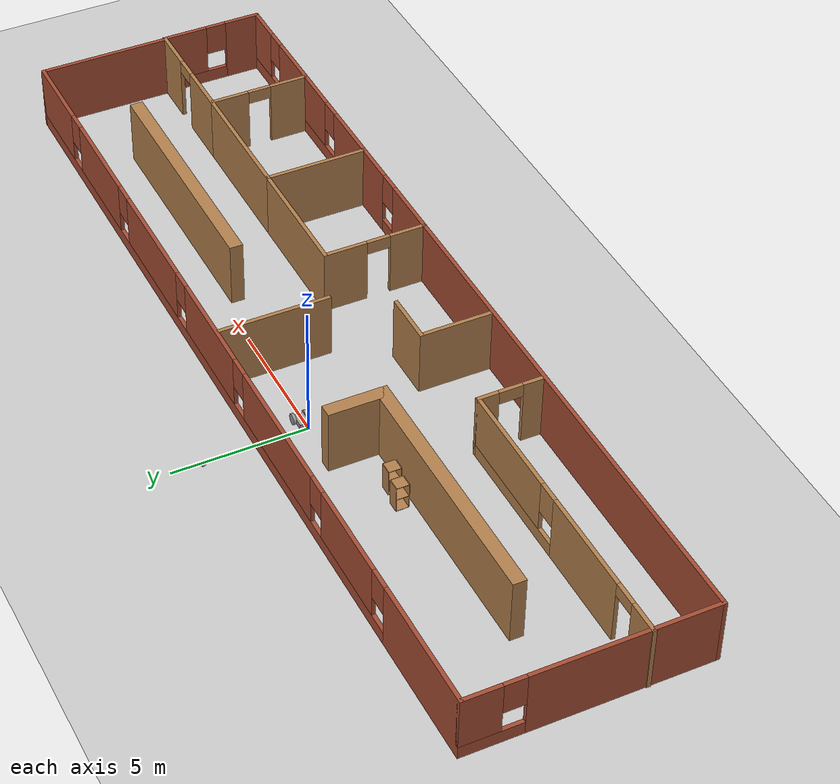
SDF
<sdf version="1.6">
 <world name="default">
  <plugin name="welcome_to_world" filename="libwelcome_to_world.so"/>
  <light name="sun" type="directional">
   <pose>0 0 10 0 -0 0</pose>
   <diffuse>0.8 0.8 0.8 1</diffuse>
   <specular>0.2 0.2 0.2 1</specular>
   <attenuation>
    <range>1000</range>
    <constant>0.9</constant>
    <linear>0.01</linear>
    <quadratic>0.001</quadratic>
   </attenuation>
   <direction>-0.5 0.1 -0.9</direction>
  </light>
  <model name="ground_plane">
   <static>1</static>
   <link name="link">
    <collision name="collision">
     <geometry><plane><normal>0 0 1</normal><size>100 100</size></plane></geometry>
     <surface>
      <contact><collide_bitmask>65535</collide_bitmask></contact>
      <friction><ode><mu>100</mu><mu2>50</mu2></ode></friction>
     </surface>
    </collision>
    <visual name="visual">
     <cast_shadows>0</cast_shadows>
     <geometry><plane><normal>0 0 1</normal><size>100 100</size></plane></geometry>
     <material>
      <script><uri>file://media/materials/scripts/gazebo.material</uri><name>Gazebo/Grey</name></script>
     </material>
    </visual>
   </link>
  </model>
  <gravity>0 0 -9.8</gravity>
  <magnetic_field>6e-06 2.3e-05 -4.2e-05</magnetic_field>
  <atmosphere type="adiabatic"/>
  <physics name="default_physics" default="0" type="ode">
   <max_step_size>0.001</max_step_size>
   <real_time_factor>1</real_time_factor>
   <real_time_update_rate>1000</real_time_update_rate>
  </physics>
  <scene><ambient>0.4 0.4 0.4 1</ambient><background>0.7 0.7 0.7 1</background><shadows>1</shadows></scene>
  <audio><device>default</device></audio>
  <spherical_coordinates>
   <surface_model>EARTH_WGS84</surface_model>
   <latitude_deg>0</latitude_deg>
   <longitude_deg>0</longitude_deg>
   <elevation>0</elevation>
   <heading_deg>0</heading_deg>
  </spherical_coordinates>
  <model name="project_1_model">
   <link name="link_0">
    <inertial>
     <mass>1</mass>
     <inertia>
      <ixx>0.166667</ixx>
      <ixy>0</ixy>
      <ixz>0</ixz>
      <iyy>0.166667</iyy>
      <iyz>0</iyz>
      <izz>0.166667</izz>
     </inertia>
    </inertial>
    <pose>-0.03625 0.03125 0.025 0 -0 0</pose>
    <visual name="visual">
     <geometry><box><size>0.55 0.35 0.2</size></box></geometry>
     <material>
      <lighting>1</lighting>
      <script><uri>file://media/materials/scripts/gazebo.material</uri><name>Gazebo/Grey</name></script>
      <shader type="vertex"><normal_map>__default__</normal_map></shader>
      <ambient>0.3 0.3 0.3 1</ambient>
      <diffuse>0.7 0.7 0.7 1</diffuse>
      <specular>0.01 0.01 0.01 1</specular>
      <emissive>0 0 0 1</emissive>
     </material>
    </visual>
    <collision name="collision">
     <pose>-0.01 0 0 0 -0 0</pose>
     <geometry><box><size>0.55 0.35 0.2</size></box></geometry>
     <surface>
      <friction>
       <ode><mu>1</mu><mu2>1</mu2><fdir1>0 0 0</fdir1><slip1>0</slip1><slip2>0</slip2></ode>
       <torsional>
        <coefficient>1</coefficient>
        <patch_radius>0</patch_radius>
        <surface_radius>0</surface_radius>
        <use_patch_radius>1</use_patch_radius>
        <ode><slip>0</slip></ode>
       </torsional>
      </friction>
      <bounce><restitution_coefficient>0</restitution_coefficient><threshold>1e+06</threshold></bounce>
      <contact>
       <collide_without_contact>0</collide_without_contact>
       <collide_without_contact_bitmask>1</collide_without_contact_bitmask>
       <collide_bitmask>1</collide_bitmask>
       <ode>
        <soft_cfm>0</soft_cfm>
        <soft_erp>0.2</soft_erp>
        <kp>1e+13</kp>
        <kd>1</kd>
        <max_vel>0.01</max_vel>
        <min_depth>0</min_depth>
       </ode>
       <bullet>
        <split_impulse>1</split_impulse>
        <split_impulse_penetration_threshold>-0.01</split_impulse_penetration_threshold>
        <soft_cfm>0</soft_cfm>
        <soft_erp>0.2</soft_erp>
        <kp>1e+13</kp>
        <kd>1</kd>
       </bullet>
      </contact>
     </surface>
    </collision>
   </link>
   <link name="link_1">
    <inertial>
     <mass>1</mass>
     <inertia><ixx>0.145833</ixx><ixy>0</ixy><ixz>0</ixz><iyy>0.145833</iyy><iyz>0</iyz><izz>0.125</izz></inertia>
    </inertial>
    <pose>0.16375 0.256269 -0.175 0 -0 0</pose>
    <visual name="visual">
     <pose>0 0 0.2 1.5707 -0 0</pose>
     <geometry><cylinder><radius>0.2</radius><length>0.1</length></cylinder></geometry>
     <material>
      <lighting>1</lighting>
      <script><uri>file://media/materials/scripts/gazebo.material</uri><name>Gazebo/Grey</name></script>
      <shader type="vertex"><normal_map>__default__</normal_map></shader>
      <ambient>0.3 0.3 0.3 1</ambient>
      <diffuse>0.7 0.7 0.7 1</diffuse>
      <specular>0.01 0.01 0.01 1</specular>
      <emissive>0 0 0 1</emissive>
     </material>
    </visual>
    <collision name="collision">
     <pose>0 0 0.2 1.5707 -0 0</pose>
     <geometry><cylinder><radius>0.2</radius><length>0.1</length></cylinder></geometry>
     <surface>
      <friction>
       <ode><mu>1</mu><mu2>1</mu2><fdir1>0 0 0</fdir1><slip1>0</slip1><slip2>0</slip2></ode>
       <torsional>
        <coefficient>1</coefficient>
        <patch_radius>0</patch_radius>
        <surface_radius>0</surface_radius>
        <use_patch_radius>1</use_patch_radius>
        <ode><slip>0</slip></ode>
       </torsional>
      </friction>
      <bounce><restitution_coefficient>0</restitution_coefficient><threshold>1e+06</threshold></bounce>
      <contact>
       <collide_without_contact>0</collide_without_contact>
       <collide_without_contact_bitmask>1</collide_without_contact_bitmask>
       <collide_bitmask>1</collide_bitmask>
       <ode>
        <soft_cfm>0</soft_cfm>
        <soft_erp>0.2</soft_erp>
        <kp>1e+13</kp>
        <kd>1</kd>
        <max_vel>0.01</max_vel>
        <min_depth>0</min_depth>
       </ode>
       <bullet>
        <split_impulse>1</split_impulse>
        <split_impulse_penetration_threshold>-0.01</split_impulse_penetration_threshold>
        <soft_cfm>0</soft_cfm>
        <soft_erp>0.2</soft_erp>
        <kp>1e+13</kp>
        <kd>1</kd>
       </bullet>
      </contact>
     </surface>
    </collision>
   </link>
   <link name="link_1_clone">
    <inertial>
     <mass>1</mass>
     <inertia><ixx>0.145833</ixx><ixy>0</ixy><ixz>0</ixz><iyy>0.145833</iyy><iyz>0</iyz><izz>0.125</izz></inertia>
    </inertial>
    <pose>0.16375 -0.193769 -0.175 0 -0 0</pose>
    <visual name="visual">
     <pose>0 0 0.2 1.5707 -0 0</pose>
     <geometry><cylinder><radius>0.2</radius><length>0.1</length></cylinder></geometry>
     <material>
      <lighting>1</lighting>
      <script><uri>file://media/materials/scripts/gazebo.material</uri><name>Gazebo/Grey</name></script>
      <shader type="vertex"><normal_map>__default__</normal_map></shader>
      <ambient>0.3 0.3 0.3 1</ambient>
      <diffuse>0.7 0.7 0.7 1</diffuse>
      <specular>0.01 0.01 0.01 1</specular>
      <emissive>0 0 0 1</emissive>
     </material>
    </visual>
    <collision name="collision">
     <pose>0 0 0.2 1.5707 -0 0</pose>
     <geometry><cylinder><radius>0.2</radius><length>0.1</length></cylinder></geometry>
     <surface>
      <friction>
       <ode><mu>1</mu><mu2>1</mu2><fdir1>0 0 0</fdir1><slip1>0</slip1><slip2>0</slip2></ode>
       <torsional>
        <coefficient>1</coefficient>
        <patch_radius>0</patch_radius>
        <surface_radius>0</surface_radius>
        <use_patch_radius>1</use_patch_radius>
        <ode><slip>0</slip></ode>
       </torsional>
      </friction>
      <bounce><restitution_coefficient>0</restitution_coefficient><threshold>1e+06</threshold></bounce>
      <contact>
       <collide_without_contact>0</collide_without_contact>
       <collide_without_contact_bitmask>1</collide_without_contact_bitmask>
       <collide_bitmask>1</collide_bitmask>
       <ode>
        <soft_cfm>0</soft_cfm>
        <soft_erp>0.2</soft_erp>
        <kp>1e+13</kp>
        <kd>1</kd>
        <max_vel>0.01</max_vel>
        <min_depth>0</min_depth>
       </ode>
       <bullet>
        <split_impulse>1</split_impulse>
        <split_impulse_penetration_threshold>-0.01</split_impulse_penetration_threshold>
        <soft_cfm>0</soft_cfm>
        <soft_erp>0.2</soft_erp>
        <kp>1e+13</kp>
        <kd>1</kd>
       </bullet>
      </contact>
     </surface>
    </collision>
   </link>
   <link name="link_2">
    <inertial>
     <mass>1</mass>
     <inertia><ixx>0.1</ixx><ixy>0</ixy><ixz>0</ixz><iyy>0.1</iyy><iyz>0</iyz><izz>0.1</izz></inertia>
    </inertial>
    <pose>-0.23625 0.03125 -0.125 0 -0 0</pose>
    <visual name="visual">
     <geometry><sphere><radius>0.05</radius></sphere></geometry>
     <material>
      <lighting>1</lighting>
      <script><uri>file://media/materials/scripts/gazebo.material</uri><name>Gazebo/Grey</name></script>
      <shader type="vertex"><normal_map>__default__</normal_map></shader>
      <ambient>0.3 0.3 0.3 1</ambient>
      <diffuse>0.7 0.7 0.7 1</diffuse>
      <specular>0.01 0.01 0.01 1</specular>
      <emissive>0 0 0 1</emissive>
     </material>
    </visual>
    <collision name="collision">
     <geometry><sphere><radius>0.05</radius></sphere></geometry>
     <surface>
      <friction>
       <ode><mu>1</mu><mu2>1</mu2><fdir1>0 0 0</fdir1><slip1>0</slip1><slip2>0</slip2></ode>
       <torsional>
        <coefficient>1</coefficient>
        <patch_radius>0</patch_radius>
        <surface_radius>0</surface_radius>
        <use_patch_radius>1</use_patch_radius>
        <ode><slip>0</slip></ode>
       </torsional>
      </friction>
      <bounce><restitution_coefficient>0</restitution_coefficient><threshold>1e+06</threshold></bounce>
      <contact>
       <collide_without_contact>0</collide_without_contact>
       <collide_without_contact_bitmask>1</collide_without_contact_bitmask>
       <collide_bitmask>1</collide_bitmask>
       <ode>
        <soft_cfm>0</soft_cfm>
        <soft_erp>0.2</soft_erp>
        <kp>1e+13</kp>
        <kd>1</kd>
        <max_vel>0.01</max_vel>
        <min_depth>0</min_depth>
       </ode>
       <bullet>
        <split_impulse>1</split_impulse>
        <split_impulse_penetration_threshold>-0.01</split_impulse_penetration_threshold>
        <soft_cfm>0</soft_cfm>
        <soft_erp>0.2</soft_erp>
        <kp>1e+13</kp>
        <kd>1</kd>
       </bullet>
      </contact>
     </surface>
    </collision>
   </link>
   <joint name="link_0_JOINT_0" type="revolute">
    <parent>link_0</parent>
    <child>link_1</child>
    <pose>0 0 0 0 -0.01 0</pose>
    <axis>
     <xyz>1 0 0</xyz>
     <use_parent_model_frame>0</use_parent_model_frame>
     <limit>
      <lower>-1.79769e+308</lower>
      <upper>1.79769e+308</upper>
      <effort>-1</effort>
      <velocity>-1</velocity>
     </limit>
     <dynamics>
      <spring_reference>0</spring_reference>
      <spring_stiffness>0</spring_stiffness>
      <damping>0</damping>
     </dynamics>
    </axis>
    <physics>
     <ode><limit><cfm>0</cfm><erp>0.2</erp></limit><suspension><cfm>0</cfm><erp>0.2</erp></suspension></ode>
    </physics>
   </joint>
   <joint name="link_0_JOINT_1" type="revolute">
    <parent>link_0</parent>
    <child>link_1_clone</child>
    <axis>
     <xyz>1 0 0</xyz>
     <use_parent_model_frame>0</use_parent_model_frame>
     <limit>
      <lower>-1.79769e+308</lower>
      <upper>1.79769e+308</upper>
      <effort>-1</effort>
      <velocity>-1</velocity>
     </limit>
     <dynamics>
      <spring_reference>0</spring_reference>
      <spring_stiffness>0</spring_stiffness>
      <damping>0</damping>
     </dynamics>
    </axis>
    <physics>
     <ode><limit><cfm>0</cfm><erp>0.2</erp></limit><suspension><cfm>0</cfm><erp>0.2</erp></suspension></ode>
    </physics>
   </joint>
   <joint name="link_0_JOINT_5" type="ball">
    <parent>link_0</parent>
    <child>link_2</child>
    <physics>
     <ode><limit><cfm>0</cfm><erp>0.2</erp></limit><suspension><cfm>0</cfm><erp>0.2</erp></suspension></ode>
    </physics>
   </joint>
   <static>0</static>
   <pose>0.300774 0.110573 0.174999 4e-06 3e-06 -0.02402</pose>
  </model>
  <model name="project_1_building">
   <pose>2.65425 -2.52692 0 0 -0 0</pose>
   <link name="Wall_103">
    <collision name="Wall_103_Collision">
     <geometry><box><size>20 0.15 2.5</size></box></geometry>
     <pose>0 0 1.25 0 -0 0</pose>
    </collision>
    <visual name="Wall_103_Visual">
     <pose>0 0 1.25 0 -0 0</pose>
     <geometry><box><size>20 0.15 2.5</size></box></geometry>
     <material>
      <script><uri>file://media/materials/scripts/gazebo.material</uri><name>Gazebo/Bricks</name></script>
      <ambient>1 1 1 1</ambient>
     </material>
     <meta><layer>0</layer></meta>
    </visual>
    <pose>-7.258 -4.425 0 0 -0 0</pose>
   </link>
   <link name="Wall_105">
    <pose>2.667 -2.5 0 0 -0 1.5708</pose>
    <visual name="Wall_105_Visual_0">
     <pose>-1.28923 0 1.25 0 -0 0</pose>
     <geometry><box><size>1.42155 0.15 2.5</size></box></geometry>
     <material>
      <script><uri>file://media/materials/scripts/gazebo.material</uri><name>Gazebo/Wood</name></script>
      <ambient>1 1 1 1</ambient>
     </material>
     <meta><layer>0</layer></meta>
    </visual>
    <collision name="Wall_105_Collision_0">
     <geometry><box><size>1.42155 0.15 2.5</size></box></geometry>
     <pose>-1.28923 0 1.25 0 -0 0</pose>
    </collision>
    <visual name="Wall_105_Visual_1">
     <pose>1.16077 0 1.25 0 -0 0</pose>
     <geometry><box><size>1.67845 0.15 2.5</size></box></geometry>
     <material>
      <script><uri>file://media/materials/scripts/gazebo.material</uri><name>Gazebo/Wood</name></script>
      <ambient>1 1 1 1</ambient>
     </material>
     <meta><layer>0</layer></meta>
    </visual>
    <collision name="Wall_105_Collision_1">
     <geometry><box><size>1.67845 0.15 2.5</size></box></geometry>
     <pose>1.16077 0 1.25 0 -0 0</pose>
    </collision>
    <visual name="Wall_105_Visual_2">
     <pose>-0.128452 0 2.25 0 -0 0</pose>
     <geometry><box><size>0.9 0.15 0.5</size></box></geometry>
     <material>
      <script><uri>file://media/materials/scripts/gazebo.material</uri><name>Gazebo/Wood</name></script>
      <ambient>1 1 1 1</ambient>
     </material>
     <meta><layer>0</layer></meta>
    </visual>
    <collision name="Wall_105_Collision_2">
     <geometry><box><size>0.9 0.15 0.5</size></box></geometry>
     <pose>-0.128452 0 2.25 0 -0 0</pose>
    </collision>
   </link>
   <link name="Wall_106">
    <collision name="Wall_106_Collision">
     <geometry><box><size>5 0.15 2.5</size></box></geometry>
     <pose>0 0 1.25 0 -0 0</pose>
    </collision>
    <visual name="Wall_106_Visual">
     <pose>0 0 1.25 0 -0 0</pose>
     <geometry><box><size>5 0.15 2.5</size></box></geometry>
     <material>
      <script><uri>file://media/materials/scripts/gazebo.material</uri><name>Gazebo/Wood</name></script>
      <ambient>1 1 1 1</ambient>
     </material>
     <meta><layer>0</layer></meta>
    </visual>
    <pose>5.092 -0.575 0 0 -0 0</pose>
   </link>
   <link name="Wall_107">
    <collision name="Wall_107_Collision">
     <geometry><box><size>4 0.15 2.5</size></box></geometry>
     <pose>0 0 1.25 0 -0 0</pose>
    </collision>
    <visual name="Wall_107_Visual">
     <pose>0 0 1.25 0 -0 0</pose>
     <geometry><box><size>4 0.15 2.5</size></box></geometry>
     <material>
      <script><uri>file://media/materials/scripts/gazebo.material</uri><name>Gazebo/Wood</name></script>
      <ambient>1 1 1 1</ambient>
     </material>
     <meta><layer>0</layer></meta>
    </visual>
    <pose>7.517 -2.5 0 0 -0 -1.5708</pose>
   </link>
   <link name="Wall_108">
    <pose>5.092 -4.425 0 0 -0 3.14159</pose>
    <visual name="Wall_108_Visual_0">
     <pose>-1.61317 0 1.25 0 -0 0</pose>
     <geometry><box><size>1.77367 0.15 2.5</size></box></geometry>
     <material>
      <script><uri>file://media/materials/scripts/gazebo.material</uri><name>Gazebo/Bricks</name></script>
      <ambient>1 1 1 1</ambient>
     </material>
     <meta><layer>0</layer></meta>
    </visual>
    <collision name="Wall_108_Collision_0">
     <geometry><box><size>1.77367 0.15 2.5</size></box></geometry>
     <pose>-1.61317 0 1.25 0 -0 0</pose>
    </collision>
    <visual name="Wall_108_Visual_1">
     <pose>0.886833 0 0.25 0 -0 0</pose>
     <geometry><box><size>3.22634 0.15 0.5</size></box></geometry>
     <material>
      <script><uri>file://media/materials/scripts/gazebo.material</uri><name>Gazebo/Bricks</name></script>
      <ambient>1 1 1 1</ambient>
     </material>
     <meta><layer>0</layer></meta>
    </visual>
    <collision name="Wall_108_Collision_1">
     <geometry><box><size>3.22634 0.15 0.5</size></box></geometry>
     <pose>0.886833 0 0.25 0 -0 0</pose>
    </collision>
    <visual name="Wall_108_Visual_2">
     <pose>1.28683 0 1.5 0 -0 0</pose>
     <geometry><box><size>2.42633 0.15 2</size></box></geometry>
     <material>
      <script><uri>file://media/materials/scripts/gazebo.material</uri><name>Gazebo/Bricks</name></script>
      <ambient>1 1 1 1</ambient>
     </material>
     <meta><layer>0</layer></meta>
    </visual>
    <collision name="Wall_108_Collision_2">
     <geometry><box><size>2.42633 0.15 2</size></box></geometry>
     <pose>1.28683 0 1.5 0 -0 0</pose>
    </collision>
    <visual name="Wall_108_Visual_3">
     <pose>-0.326335 0 1.9 0 -0 0</pose>
     <geometry><box><size>0.8 0.15 1.2</size></box></geometry>
     <material>
      <script><uri>file://media/materials/scripts/gazebo.material</uri><name>Gazebo/Bricks</name></script>
      <ambient>1 1 1 1</ambient>
     </material>
     <meta><layer>0</layer></meta>
    </visual>
    <collision name="Wall_108_Collision_3">
     <geometry><box><size>0.8 0.15 1.2</size></box></geometry>
     <pose>-0.326335 0 1.9 0 -0 0</pose>
    </collision>
   </link>
   <link name="Wall_110">
    <pose>10.067 -4.425 0 0 -0 0</pose>
    <visual name="Wall_110_Visual_0">
     <pose>-1.37302 0 1.25 0 -0 0</pose>
     <geometry><box><size>2.50397 0.15 2.5</size></box></geometry>
     <material>
      <script><uri>file://media/materials/scripts/gazebo.material</uri><name>Gazebo/Bricks</name></script>
      <ambient>1 1 1 1</ambient>
     </material>
     <meta><layer>0</layer></meta>
    </visual>
    <collision name="Wall_110_Collision_0">
     <geometry><box><size>2.50397 0.15 2.5</size></box></geometry>
     <pose>-1.37302 0 1.25 0 -0 0</pose>
    </collision>
    <visual name="Wall_110_Visual_1">
     <pose>1.25198 0 0.25 0 -0 0</pose>
     <geometry><box><size>2.74603 0.15 0.5</size></box></geometry>
     <material>
      <script><uri>file://media/materials/scripts/gazebo.material</uri><name>Gazebo/Bricks</name></script>
      <ambient>1 1 1 1</ambient>
     </material>
     <meta><layer>0</layer></meta>
    </visual>
    <collision name="Wall_110_Collision_1">
     <geometry><box><size>2.74603 0.15 0.5</size></box></geometry>
     <pose>1.25198 0 0.25 0 -0 0</pose>
    </collision>
    <visual name="Wall_110_Visual_2">
     <pose>1.65199 0 1.5 0 -0 0</pose>
     <geometry><box><size>1.94603 0.15 2</size></box></geometry>
     <material>
      <script><uri>file://media/materials/scripts/gazebo.material</uri><name>Gazebo/Bricks</name></script>
      <ambient>1 1 1 1</ambient>
     </material>
     <meta><layer>0</layer></meta>
    </visual>
    <collision name="Wall_110_Collision_2">
     <geometry><box><size>1.94603 0.15 2</size></box></geometry>
     <pose>1.65199 0 1.5 0 -0 0</pose>
    </collision>
    <visual name="Wall_110_Visual_3">
     <pose>0.27897 0 1.9 0 -0 0</pose>
     <geometry><box><size>0.8 0.15 1.2</size></box></geometry>
     <material>
      <script><uri>file://media/materials/scripts/gazebo.material</uri><name>Gazebo/Bricks</name></script>
      <ambient>1 1 1 1</ambient>
     </material>
     <meta><layer>0</layer></meta>
    </visual>
    <collision name="Wall_110_Collision_3">
     <geometry><box><size>0.8 0.15 1.2</size></box></geometry>
     <pose>0.27897 0 1.9 0 -0 0</pose>
    </collision>
   </link>
   <link name="Wall_111">
    <pose>12.617 -2.5 0 0 -0 1.5708</pose>
    <visual name="Wall_111_Visual_0">
     <pose>-1.21927 0 1.25 0 -0 0</pose>
     <geometry><box><size>1.56147 0.15 2.5</size></box></geometry>
     <material>
      <script><uri>file://media/materials/scripts/gazebo.material</uri><name>Gazebo/Wood</name></script>
      <ambient>1 1 1 1</ambient>
     </material>
     <meta><layer>0</layer></meta>
    </visual>
    <collision name="Wall_111_Collision_0">
     <geometry><box><size>1.56147 0.15 2.5</size></box></geometry>
     <pose>-1.21927 0 1.25 0 -0 0</pose>
    </collision>
    <visual name="Wall_111_Visual_1">
     <pose>1.23073 0 1.25 0 -0 0</pose>
     <geometry><box><size>1.53853 0.15 2.5</size></box></geometry>
     <material>
      <script><uri>file://media/materials/scripts/gazebo.material</uri><name>Gazebo/Wood</name></script>
      <ambient>1 1 1 1</ambient>
     </material>
     <meta><layer>0</layer></meta>
    </visual>
    <collision name="Wall_111_Collision_1">
     <geometry><box><size>1.53853 0.15 2.5</size></box></geometry>
     <pose>1.23073 0 1.25 0 -0 0</pose>
    </collision>
    <visual name="Wall_111_Visual_2">
     <pose>0.011469 0 2.25 0 -0 0</pose>
     <geometry><box><size>0.9 0.15 0.5</size></box></geometry>
     <material>
      <script><uri>file://media/materials/scripts/gazebo.material</uri><name>Gazebo/Wood</name></script>
      <ambient>1 1 1 1</ambient>
     </material>
     <meta><layer>0</layer></meta>
    </visual>
    <collision name="Wall_111_Collision_2">
     <geometry><box><size>0.9 0.15 0.5</size></box></geometry>
     <pose>0.011469 0 2.25 0 -0 0</pose>
    </collision>
   </link>
   <link name="Wall_112">
    <collision name="Wall_112_Collision">
     <geometry><box><size>5.25 0.15 2.5</size></box></geometry>
     <pose>0 0 1.25 0 -0 0</pose>
    </collision>
    <visual name="Wall_112_Visual">
     <pose>0 0 1.25 0 -0 0</pose>
     <geometry><box><size>5.25 0.15 2.5</size></box></geometry>
     <material>
      <script><uri>file://media/materials/scripts/gazebo.material</uri><name>Gazebo/Wood</name></script>
      <ambient>1 1 1 1</ambient>
     </material>
     <meta><layer>0</layer></meta>
    </visual>
    <pose>10.067 -0.575 0 0 -0 3.14159</pose>
   </link>
   <link name="Wall_114">
    <pose>14.917 -4.425 0 0 -0 0</pose>
    <visual name="Wall_114_Visual_0">
     <pose>-1.19399 0 1.25 0 -0 0</pose>
     <geometry><box><size>2.36202 0.15 2.5</size></box></geometry>
     <material>
      <script><uri>file://media/materials/scripts/gazebo.material</uri><name>Gazebo/Bricks</name></script>
      <ambient>1 1 1 1</ambient>
     </material>
     <meta><layer>0</layer></meta>
    </visual>
    <collision name="Wall_114_Collision_0">
     <geometry><box><size>2.36202 0.15 2.5</size></box></geometry>
     <pose>-1.19399 0 1.25 0 -0 0</pose>
    </collision>
    <visual name="Wall_114_Visual_1">
     <pose>1.18101 0 0.25 0 -0 0</pose>
     <geometry><box><size>2.38798 0.15 0.5</size></box></geometry>
     <material>
      <script><uri>file://media/materials/scripts/gazebo.material</uri><name>Gazebo/Bricks</name></script>
      <ambient>1 1 1 1</ambient>
     </material>
     <meta><layer>0</layer></meta>
    </visual>
    <collision name="Wall_114_Collision_1">
     <geometry><box><size>2.38798 0.15 0.5</size></box></geometry>
     <pose>1.18101 0 0.25 0 -0 0</pose>
    </collision>
    <visual name="Wall_114_Visual_2">
     <pose>1.58101 0 1.5 0 -0 0</pose>
     <geometry><box><size>1.58798 0.15 2</size></box></geometry>
     <material>
      <script><uri>file://media/materials/scripts/gazebo.material</uri><name>Gazebo/Bricks</name></script>
      <ambient>1 1 1 1</ambient>
     </material>
     <meta><layer>0</layer></meta>
    </visual>
    <collision name="Wall_114_Collision_2">
     <geometry><box><size>1.58798 0.15 2</size></box></geometry>
     <pose>1.58101 0 1.5 0 -0 0</pose>
    </collision>
    <visual name="Wall_114_Visual_3">
     <pose>0.387023 0 1.9 0 -0 0</pose>
     <geometry><box><size>0.8 0.15 1.2</size></box></geometry>
     <material>
      <script><uri>file://media/materials/scripts/gazebo.material</uri><name>Gazebo/Bricks</name></script>
      <ambient>1 1 1 1</ambient>
     </material>
     <meta><layer>0</layer></meta>
    </visual>
    <collision name="Wall_114_Collision_3">
     <geometry><box><size>0.8 0.15 1.2</size></box></geometry>
     <pose>0.387023 0 1.9 0 -0 0</pose>
    </collision>
   </link>
   <link name="Wall_115">
    <pose>17.217 -2.5 0 0 -0 1.5708</pose>
    <visual name="Wall_115_Visual_0">
     <pose>-1.28817 0 1.25 0 -0 0</pose>
     <geometry><box><size>1.42366 0.15 2.5</size></box></geometry>
     <material>
      <script><uri>file://media/materials/scripts/gazebo.material</uri><name>Gazebo/Bricks</name></script>
      <ambient>1 1 1 1</ambient>
     </material>
     <meta><layer>0</layer></meta>
    </visual>
    <collision name="Wall_115_Collision_0">
     <geometry><box><size>1.42366 0.15 2.5</size></box></geometry>
     <pose>-1.28817 0 1.25 0 -0 0</pose>
    </collision>
    <visual name="Wall_115_Visual_1">
     <pose>0.711831 0 0.25 0 -0 0</pose>
     <geometry><box><size>2.57634 0.15 0.5</size></box></geometry>
     <material>
      <script><uri>file://media/materials/scripts/gazebo.material</uri><name>Gazebo/Bricks</name></script>
      <ambient>1 1 1 1</ambient>
     </material>
     <meta><layer>0</layer></meta>
    </visual>
    <collision name="Wall_115_Collision_1">
     <geometry><box><size>2.57634 0.15 0.5</size></box></geometry>
     <pose>0.711831 0 0.25 0 -0 0</pose>
    </collision>
    <visual name="Wall_115_Visual_2">
     <pose>1.11183 0 1.5 0 -0 0</pose>
     <geometry><box><size>1.77634 0.15 2</size></box></geometry>
     <material>
      <script><uri>file://media/materials/scripts/gazebo.material</uri><name>Gazebo/Bricks</name></script>
      <ambient>1 1 1 1</ambient>
     </material>
     <meta><layer>0</layer></meta>
    </visual>
    <collision name="Wall_115_Collision_2">
     <geometry><box><size>1.77634 0.15 2</size></box></geometry>
     <pose>1.11183 0 1.5 0 -0 0</pose>
    </collision>
    <visual name="Wall_115_Visual_3">
     <pose>-0.176337 0 1.9 0 -0 0</pose>
     <geometry><box><size>0.8 0.15 1.2</size></box></geometry>
     <material>
      <script><uri>file://media/materials/scripts/gazebo.material</uri><name>Gazebo/Bricks</name></script>
      <ambient>1 1 1 1</ambient>
     </material>
     <meta><layer>0</layer></meta>
    </visual>
    <collision name="Wall_115_Collision_3">
     <geometry><box><size>0.8 0.15 1.2</size></box></geometry>
     <pose>-0.176337 0 1.9 0 -0 0</pose>
    </collision>
   </link>
   <link name="Wall_116">
    <pose>14.917 -0.575 0 0 -0 3.14159</pose>
    <visual name="Wall_116_Visual_0">
     <pose>-1.48883 0 1.25 0 -0 0</pose>
     <geometry><box><size>1.77234 0.15 2.5</size></box></geometry>
     <material>
      <script><uri>file://media/materials/scripts/gazebo.material</uri><name>Gazebo/Wood</name></script>
      <ambient>1 1 1 1</ambient>
     </material>
     <meta><layer>0</layer></meta>
    </visual>
    <collision name="Wall_116_Collision_0">
     <geometry><box><size>1.77234 0.15 2.5</size></box></geometry>
     <pose>-1.48883 0 1.25 0 -0 0</pose>
    </collision>
    <visual name="Wall_116_Visual_1">
     <pose>1.33617 0 1.25 0 -0 0</pose>
     <geometry><box><size>2.07766 0.15 2.5</size></box></geometry>
     <material>
      <script><uri>file://media/materials/scripts/gazebo.material</uri><name>Gazebo/Wood</name></script>
      <ambient>1 1 1 1</ambient>
     </material>
     <meta><layer>0</layer></meta>
    </visual>
    <collision name="Wall_116_Collision_1">
     <geometry><box><size>2.07766 0.15 2.5</size></box></geometry>
     <pose>1.33617 0 1.25 0 -0 0</pose>
    </collision>
    <visual name="Wall_116_Visual_2">
     <pose>-0.152657 0 2.25 0 -0 0</pose>
     <geometry><box><size>0.9 0.15 0.5</size></box></geometry>
     <material>
      <script><uri>file://media/materials/scripts/gazebo.material</uri><name>Gazebo/Wood</name></script>
      <ambient>1 1 1 1</ambient>
     </material>
     <meta><layer>0</layer></meta>
    </visual>
    <collision name="Wall_116_Collision_2">
     <geometry><box><size>0.9 0.15 0.5</size></box></geometry>
     <pose>-0.152657 0 2.25 0 -0 0</pose>
    </collision>
   </link>
   <link name="Wall_119">
    <pose>-17.183 -0 0 0 -0 1.5708</pose>
    <visual name="Wall_119_Visual_0">
     <pose>-1.12664 0 1.25 0 -0 0</pose>
     <geometry><box><size>6.74672 0.15 2.5</size></box></geometry>
     <material>
      <script><uri>file://media/materials/scripts/gazebo.material</uri><name>Gazebo/Bricks</name></script>
      <ambient>1 1 1 1</ambient>
     </material>
     <meta><layer>0</layer></meta>
    </visual>
    <collision name="Wall_119_Collision_0">
     <geometry><box><size>6.74672 0.15 2.5</size></box></geometry>
     <pose>-1.12664 0 1.25 0 -0 0</pose>
    </collision>
    <visual name="Wall_119_Visual_1">
     <pose>3.37336 0 0.25 0 -0 0</pose>
     <geometry><box><size>2.25327 0.15 0.5</size></box></geometry>
     <material>
      <script><uri>file://media/materials/scripts/gazebo.material</uri><name>Gazebo/Bricks</name></script>
      <ambient>1 1 1 1</ambient>
     </material>
     <meta><layer>0</layer></meta>
    </visual>
    <collision name="Wall_119_Collision_1">
     <geometry><box><size>2.25327 0.15 0.5</size></box></geometry>
     <pose>3.37336 0 0.25 0 -0 0</pose>
    </collision>
    <visual name="Wall_119_Visual_2">
     <pose>3.77336 0 1.5 0 -0 0</pose>
     <geometry><box><size>1.45328 0.15 2</size></box></geometry>
     <material>
      <script><uri>file://media/materials/scripts/gazebo.material</uri><name>Gazebo/Bricks</name></script>
      <ambient>1 1 1 1</ambient>
     </material>
     <meta><layer>0</layer></meta>
    </visual>
    <collision name="Wall_119_Collision_2">
     <geometry><box><size>1.45328 0.15 2</size></box></geometry>
     <pose>3.77336 0 1.5 0 -0 0</pose>
    </collision>
    <visual name="Wall_119_Visual_3">
     <pose>2.64672 0 1.9 0 -0 0</pose>
     <geometry><box><size>0.8 0.15 1.2</size></box></geometry>
     <material>
      <script><uri>file://media/materials/scripts/gazebo.material</uri><name>Gazebo/Bricks</name></script>
      <ambient>1 1 1 1</ambient>
     </material>
     <meta><layer>0</layer></meta>
    </visual>
    <collision name="Wall_119_Collision_3">
     <geometry><box><size>0.8 0.15 1.2</size></box></geometry>
     <pose>2.64672 0 1.9 0 -0 0</pose>
    </collision>
   </link>
   <link name="Wall_120">
    <pose>-0.008001 4.425 0 0 -0 0</pose>
    <visual name="Wall_120_Visual_0">
     <pose>-14.7732 0 1.25 0 -0 0</pose>
     <geometry><box><size>4.95359 0.15 2.5</size></box></geometry>
     <material>
      <script><uri>file://media/materials/scripts/gazebo.material</uri><name>Gazebo/Bricks</name></script>
      <ambient>1 1 1 1</ambient>
     </material>
     <meta><layer>0</layer></meta>
    </visual>
    <collision name="Wall_120_Collision_0">
     <geometry><box><size>4.95359 0.15 2.5</size></box></geometry>
     <pose>-14.7732 0 1.25 0 -0 0</pose>
    </collision>
    <visual name="Wall_120_Visual_1">
     <pose>2.4768 0 0.25 0 -0 0</pose>
     <geometry><box><size>29.5464 0.15 0.5</size></box></geometry>
     <material>
      <script><uri>file://media/materials/scripts/gazebo.material</uri><name>Gazebo/Bricks</name></script>
      <ambient>1 1 1 1</ambient>
     </material>
     <meta><layer>0</layer></meta>
    </visual>
    <collision name="Wall_120_Collision_1">
     <geometry><box><size>29.5464 0.15 0.5</size></box></geometry>
     <pose>2.4768 0 0.25 0 -0 0</pose>
    </collision>
    <visual name="Wall_120_Visual_2">
     <pose>-9.67517 0 1.5 0 -0 0</pose>
     <geometry><box><size>3.64248 0.15 2</size></box></geometry>
     <material>
      <script><uri>file://media/materials/scripts/gazebo.material</uri><name>Gazebo/Bricks</name></script>
      <ambient>1 1 1 1</ambient>
     </material>
     <meta><layer>0</layer></meta>
    </visual>
    <collision name="Wall_120_Collision_2">
     <geometry><box><size>3.64248 0.15 2</size></box></geometry>
     <pose>-9.67517 0 1.5 0 -0 0</pose>
    </collision>
    <visual name="Wall_120_Visual_3">
     <pose>-4.40535 0 1.5 0 -0 0</pose>
     <geometry><box><size>5.29716 0.15 2</size></box></geometry>
     <material>
      <script><uri>file://media/materials/scripts/gazebo.material</uri><name>Gazebo/Bricks</name></script>
      <ambient>1 1 1 1</ambient>
     </material>
     <meta><layer>0</layer></meta>
    </visual>
    <collision name="Wall_120_Collision_3">
     <geometry><box><size>5.29716 0.15 2</size></box></geometry>
     <pose>-4.40535 0 1.5 0 -0 0</pose>
    </collision>
    <visual name="Wall_120_Visual_4">
     <pose>1.10705 0 1.5 0 -0 0</pose>
     <geometry><box><size>4.12763 0.15 2</size></box></geometry>
     <material>
      <script><uri>file://media/materials/scripts/gazebo.material</uri><name>Gazebo/Bricks</name></script>
      <ambient>1 1 1 1</ambient>
     </material>
     <meta><layer>0</layer></meta>
    </visual>
    <collision name="Wall_120_Collision_4">
     <geometry><box><size>4.12763 0.15 2</size></box></geometry>
     <pose>1.10705 0 1.5 0 -0 0</pose>
    </collision>
    <visual name="Wall_120_Visual_5">
     <pose>6.24761 0 1.5 0 -0 0</pose>
     <geometry><box><size>4.55348 0.15 2</size></box></geometry>
     <material>
      <script><uri>file://media/materials/scripts/gazebo.material</uri><name>Gazebo/Bricks</name></script>
      <ambient>1 1 1 1</ambient>
     </material>
     <meta><layer>0</layer></meta>
    </visual>
    <collision name="Wall_120_Collision_5">
     <geometry><box><size>4.55348 0.15 2</size></box></geometry>
     <pose>6.24761 0 1.5 0 -0 0</pose>
    </collision>
    <visual name="Wall_120_Visual_6">
     <pose>11.2817 0 1.5 0 -0 0</pose>
     <geometry><box><size>3.91471 0.15 2</size></box></geometry>
     <material>
      <script><uri>file://media/materials/scripts/gazebo.material</uri><name>Gazebo/Bricks</name></script>
      <ambient>1 1 1 1</ambient>
     </material>
     <meta><layer>0</layer></meta>
    </visual>
    <collision name="Wall_120_Collision_6">
     <geometry><box><size>3.91471 0.15 2</size></box></geometry>
     <pose>11.2817 0 1.5 0 -0 0</pose>
    </collision>
    <visual name="Wall_120_Visual_7">
     <pose>15.6445 0 1.5 0 -0 0</pose>
     <geometry><box><size>3.21094 0.15 2</size></box></geometry>
     <material>
      <script><uri>file://media/materials/scripts/gazebo.material</uri><name>Gazebo/Bricks</name></script>
      <ambient>1 1 1 1</ambient>
     </material>
     <meta><layer>0</layer></meta>
    </visual>
    <collision name="Wall_120_Collision_7">
     <geometry><box><size>3.21094 0.15 2</size></box></geometry>
     <pose>15.6445 0 1.5 0 -0 0</pose>
    </collision>
    <visual name="Wall_120_Visual_8">
     <pose>-11.8964 0 1.9 0 -0 0</pose>
     <geometry><box><size>0.8 0.15 1.2</size></box></geometry>
     <material>
      <script><uri>file://media/materials/scripts/gazebo.material</uri><name>Gazebo/Bricks</name></script>
      <ambient>1 1 1 1</ambient>
     </material>
     <meta><layer>0</layer></meta>
    </visual>
    <collision name="Wall_120_Collision_8">
     <geometry><box><size>0.8 0.15 1.2</size></box></geometry>
     <pose>-11.8964 0 1.9 0 -0 0</pose>
    </collision>
    <visual name="Wall_120_Visual_9">
     <pose>-7.45393 0 1.9 0 -0 0</pose>
     <geometry><box><size>0.8 0.15 1.2</size></box></geometry>
     <material>
      <script><uri>file://media/materials/scripts/gazebo.material</uri><name>Gazebo/Bricks</name></script>
      <ambient>1 1 1 1</ambient>
     </material>
     <meta><layer>0</layer></meta>
    </visual>
    <collision name="Wall_120_Collision_9">
     <geometry><box><size>0.8 0.15 1.2</size></box></geometry>
     <pose>-7.45393 0 1.9 0 -0 0</pose>
    </collision>
    <visual name="Wall_120_Visual_10">
     <pose>-1.35677 0 1.9 0 -0 0</pose>
     <geometry><box><size>0.8 0.15 1.2</size></box></geometry>
     <material>
      <script><uri>file://media/materials/scripts/gazebo.material</uri><name>Gazebo/Bricks</name></script>
      <ambient>1 1 1 1</ambient>
     </material>
     <meta><layer>0</layer></meta>
    </visual>
    <collision name="Wall_120_Collision_10">
     <geometry><box><size>0.8 0.15 1.2</size></box></geometry>
     <pose>-1.35677 0 1.9 0 -0 0</pose>
    </collision>
    <visual name="Wall_120_Visual_11">
     <pose>3.57087 0 1.9 0 -0 0</pose>
     <geometry><box><size>0.8 0.15 1.2</size></box></geometry>
     <material>
      <script><uri>file://media/materials/scripts/gazebo.material</uri><name>Gazebo/Bricks</name></script>
      <ambient>1 1 1 1</ambient>
     </material>
     <meta><layer>0</layer></meta>
    </visual>
    <collision name="Wall_120_Collision_11">
     <geometry><box><size>0.8 0.15 1.2</size></box></geometry>
     <pose>3.57087 0 1.9 0 -0 0</pose>
    </collision>
    <visual name="Wall_120_Visual_12">
     <pose>8.92435 0 1.9 0 -0 0</pose>
     <geometry><box><size>0.8 0.15 1.2</size></box></geometry>
     <material>
      <script><uri>file://media/materials/scripts/gazebo.material</uri><name>Gazebo/Bricks</name></script>
      <ambient>1 1 1 1</ambient>
     </material>
     <meta><layer>0</layer></meta>
    </visual>
    <collision name="Wall_120_Collision_12">
     <geometry><box><size>0.8 0.15 1.2</size></box></geometry>
     <pose>8.92435 0 1.9 0 -0 0</pose>
    </collision>
    <visual name="Wall_120_Visual_13">
     <pose>13.6391 0 1.9 0 -0 0</pose>
     <geometry><box><size>0.8 0.15 1.2</size></box></geometry>
     <material>
      <script><uri>file://media/materials/scripts/gazebo.material</uri><name>Gazebo/Bricks</name></script>
      <ambient>1 1 1 1</ambient>
     </material>
     <meta><layer>0</layer></meta>
    </visual>
    <collision name="Wall_120_Collision_13">
     <geometry><box><size>0.8 0.15 1.2</size></box></geometry>
     <pose>13.6391 0 1.9 0 -0 0</pose>
    </collision>
   </link>
   <link name="Wall_121">
    <collision name="Wall_121_Collision">
     <geometry><box><size>5 0.15 2.5</size></box></geometry>
     <pose>0 0 1.25 0 -0 0</pose>
    </collision>
    <visual name="Wall_121_Visual">
     <pose>0 0 1.25 0 -0 0</pose>
     <geometry><box><size>5 0.15 2.5</size></box></geometry>
     <material>
      <script><uri>file://media/materials/scripts/gazebo.material</uri><name>Gazebo/Bricks</name></script>
      <ambient>1 1 1 1</ambient>
     </material>
     <meta><layer>0</layer></meta>
    </visual>
    <pose>17.167 2 0 0 -0 -1.5708</pose>
   </link>
   <link name="Wall_123">
    <collision name="Wall_123_Collision">
     <geometry><box><size>9.59951 0.5 2.5</size></box></geometry>
     <pose>0 0 1.25 0 -0 0</pose>
    </collision>
    <visual name="Wall_123_Visual">
     <pose>0 0 1.25 0 -0 0</pose>
     <geometry><box><size>9.59951 0.5 2.5</size></box></geometry>
     <material>
      <script><uri>file://media/materials/scripts/gazebo.material</uri><name>Gazebo/Wood</name></script>
      <ambient>1 1 1 1</ambient>
     </material>
     <meta><layer>0</layer></meta>
    </visual>
    <pose>-9.06356 0.694511 0 0 -0 0</pose>
   </link>
   <link name="Wall_124">
    <collision name="Wall_124_Collision">
     <geometry><box><size>2.35015 0.5 2.5</size></box></geometry>
     <pose>0 0 1.25 0 -0 0</pose>
    </collision>
    <visual name="Wall_124_Visual">
     <pose>0 0 1.25 0 -0 0</pose>
     <geometry><box><size>2.35015 0.5 2.5</size></box></geometry>
     <material>
      <script><uri>file://media/materials/scripts/gazebo.material</uri><name>Gazebo/Wood</name></script>
      <ambient>1 1 1 1</ambient>
     </material>
     <meta><layer>0</layer></meta>
    </visual>
    <pose>-4.51356 1.61951 0 0 -0 1.5708</pose>
   </link>
   <link name="Wall_126">
    <collision name="Wall_126_Collision">
     <geometry><box><size>9.35014 0.5 2.5</size></box></geometry>
     <pose>0 0 1.25 0 -0 0</pose>
    </collision>
    <visual name="Wall_126_Visual">
     <pose>0 0 1.25 0 -0 0</pose>
     <geometry><box><size>9.35014 0.5 2.5</size></box></geometry>
     <material>
      <script><uri>file://media/materials/scripts/gazebo.material</uri><name>Gazebo/Wood</name></script>
      <ambient>1 1 1 1</ambient>
     </material>
     <meta><layer>0</layer></meta>
    </visual>
    <pose>9.07044 2.02351 0 0 -0 0</pose>
   </link>
   <link name="Wall_129">
    <pose>-11.667 -1.96383 0 0 -0 0</pose>
    <visual name="Wall_129_Visual_0">
     <pose>-5.00796 0 1.25 0 -0 0</pose>
     <geometry><box><size>1.23409 0.15 2.5</size></box></geometry>
     <material>
      <script><uri>file://media/materials/scripts/gazebo.material</uri><name>Gazebo/Wood</name></script>
      <ambient>1 1 1 1</ambient>
     </material>
     <meta><layer>0</layer></meta>
    </visual>
    <collision name="Wall_129_Collision_0">
     <geometry><box><size>1.23409 0.15 2.5</size></box></geometry>
     <pose>-5.00796 0 1.25 0 -0 0</pose>
    </collision>
    <visual name="Wall_129_Visual_1">
     <pose>-1.53947 0 1.25 0 -0 0</pose>
     <geometry><box><size>3.90289 0.15 2.5</size></box></geometry>
     <material>
      <script><uri>file://media/materials/scripts/gazebo.material</uri><name>Gazebo/Wood</name></script>
      <ambient>1 1 1 1</ambient>
     </material>
     <meta><layer>0</layer></meta>
    </visual>
    <collision name="Wall_129_Collision_1">
     <geometry><box><size>3.90289 0.15 2.5</size></box></geometry>
     <pose>-1.53947 0 1.25 0 -0 0</pose>
    </collision>
    <visual name="Wall_129_Visual_2">
     <pose>3.01849 0 0.25 0 -0 0</pose>
     <geometry><box><size>5.21303 0.15 0.5</size></box></geometry>
     <material>
      <script><uri>file://media/materials/scripts/gazebo.material</uri><name>Gazebo/Wood</name></script>
      <ambient>1 1 1 1</ambient>
     </material>
     <meta><layer>0</layer></meta>
    </visual>
    <collision name="Wall_129_Collision_2">
     <geometry><box><size>5.21303 0.15 0.5</size></box></geometry>
     <pose>3.01849 0 0.25 0 -0 0</pose>
    </collision>
    <visual name="Wall_129_Visual_3">
     <pose>3.41849 0 1.5 0 -0 0</pose>
     <geometry><box><size>4.41303 0.15 2</size></box></geometry>
     <material>
      <script><uri>file://media/materials/scripts/gazebo.material</uri><name>Gazebo/Wood</name></script>
      <ambient>1 1 1 1</ambient>
     </material>
     <meta><layer>0</layer></meta>
    </visual>
    <collision name="Wall_129_Collision_3">
     <geometry><box><size>4.41303 0.15 2</size></box></geometry>
     <pose>3.41849 0 1.5 0 -0 0</pose>
    </collision>
    <visual name="Wall_129_Visual_4">
     <pose>0.811972 0 1.9 0 -0 0</pose>
     <geometry><box><size>0.8 0.15 1.2</size></box></geometry>
     <material>
      <script><uri>file://media/materials/scripts/gazebo.material</uri><name>Gazebo/Wood</name></script>
      <ambient>1 1 1 1</ambient>
     </material>
     <meta><layer>0</layer></meta>
    </visual>
    <collision name="Wall_129_Collision_4">
     <geometry><box><size>0.8 0.15 1.2</size></box></geometry>
     <pose>0.811972 0 1.9 0 -0 0</pose>
    </collision>
    <visual name="Wall_129_Visual_5">
     <pose>-3.94091 0 2.25 0 -0 0</pose>
     <geometry><box><size>0.9 0.15 0.5</size></box></geometry>
     <material>
      <script><uri>file://media/materials/scripts/gazebo.material</uri><name>Gazebo/Wood</name></script>
      <ambient>1 1 1 1</ambient>
     </material>
     <meta><layer>0</layer></meta>
    </visual>
    <collision name="Wall_129_Collision_5">
     <geometry><box><size>0.9 0.15 0.5</size></box></geometry>
     <pose>-3.94091 0 2.25 0 -0 0</pose>
    </collision>
   </link>
   <link name="Wall_130">
    <pose>-6.117 -3.13883 0 0 -0 -1.5708</pose>
    <visual name="Wall_130_Visual_0">
     <pose>-0.842838 0 1.25 0 -0 0</pose>
     <geometry><box><size>0.814324 0.15 2.5</size></box></geometry>
     <material>
      <script><uri>file://media/materials/scripts/gazebo.material</uri><name>Gazebo/Wood</name></script>
      <ambient>1 1 1 1</ambient>
     </material>
     <meta><layer>0</layer></meta>
    </visual>
    <collision name="Wall_130_Collision_0">
     <geometry><box><size>0.814324 0.15 2.5</size></box></geometry>
     <pose>-0.842838 0 1.25 0 -0 0</pose>
    </collision>
    <visual name="Wall_130_Visual_1">
     <pose>0.857162 0 1.25 0 -0 0</pose>
     <geometry><box><size>0.785676 0.15 2.5</size></box></geometry>
     <material>
      <script><uri>file://media/materials/scripts/gazebo.material</uri><name>Gazebo/Wood</name></script>
      <ambient>1 1 1 1</ambient>
     </material>
     <meta><layer>0</layer></meta>
    </visual>
    <collision name="Wall_130_Collision_1">
     <geometry><box><size>0.785676 0.15 2.5</size></box></geometry>
     <pose>0.857162 0 1.25 0 -0 0</pose>
    </collision>
    <visual name="Wall_130_Visual_2">
     <pose>0.014324 0 2.25 0 -0 0</pose>
     <geometry><box><size>0.9 0.15 0.5</size></box></geometry>
     <material>
      <script><uri>file://media/materials/scripts/gazebo.material</uri><name>Gazebo/Wood</name></script>
      <ambient>1 1 1 1</ambient>
     </material>
     <meta><layer>0</layer></meta>
    </visual>
    <collision name="Wall_130_Collision_2">
     <geometry><box><size>0.9 0.15 0.5</size></box></geometry>
     <pose>0.014324 0 2.25 0 -0 0</pose>
    </collision>
   </link>
   <link name="Wall_132">
    <collision name="Wall_132_Collision">
     <geometry><box><size>4.25 0.15 2.5</size></box></geometry>
     <pose>0 0 1.25 0 -0 0</pose>
    </collision>
    <visual name="Wall_132_Visual">
     <pose>0 0 1.25 0 -0 0</pose>
     <geometry><box><size>4.25 0.15 2.5</size></box></geometry>
     <material>
      <script><uri>file://media/materials/scripts/gazebo.material</uri><name>Gazebo/Wood</name></script>
      <ambient>1 1 1 1</ambient>
     </material>
     <meta><layer>0</layer></meta>
    </visual>
    <pose>0.56643 2.32665 0 0 -0 -1.5708</pose>
   </link>
   <link name="Wall_134">
    <collision name="Wall_134_Collision">
     <geometry><box><size>2.75 0.15 2.5</size></box></geometry>
     <pose>0 0 1.25 0 -0 0</pose>
    </collision>
    <visual name="Wall_134_Visual">
     <pose>0 0 1.25 0 -0 0</pose>
     <geometry><box><size>2.75 0.15 2.5</size></box></geometry>
     <material>
      <script><uri>file://media/materials/scripts/gazebo.material</uri><name>Gazebo/Wood</name></script>
      <ambient>1 1 1 1</ambient>
     </material>
     <meta><layer>0</layer></meta>
    </visual>
    <pose>-2.51182 -2.99842 0 0 -0 1.5708</pose>
   </link>
   <link name="Wall_135">
    <collision name="Wall_135_Collision">
     <geometry><box><size>2 0.15 2.5</size></box></geometry>
     <pose>0 0 1.25 0 -0 0</pose>
    </collision>
    <visual name="Wall_135_Visual">
     <pose>0 0 1.25 0 -0 0</pose>
     <geometry><box><size>2 0.15 2.5</size></box></geometry>
     <material>
      <script><uri>file://media/materials/scripts/gazebo.material</uri><name>Gazebo/Wood</name></script>
      <ambient>1 1 1 1</ambient>
     </material>
     <meta><layer>0</layer></meta>
    </visual>
    <pose>-1.58682 -1.69842 0 0 -0 0</pose>
   </link>
   <static>1</static>
  </model>
  <model name="cabinet">
   <static>1</static>
   <link name="cabinet_bottom_plate">
    <inertial>
     <pose>0 0 -1 0 -0 0</pose>
     <inertia><ixx>2.05</ixx><ixy>0</ixy><ixz>0</ixz><iyy>2.05</iyy><iyz>0</iyz><izz>2.05</izz></inertia>
     <mass>25</mass>
    </inertial>
    <collision name="cabinet_bottom_plate_geom">
     <pose>0 0 0.01 0 -0 0</pose>
     <geometry><box><size>0.45 0.45 0.02</size></box></geometry>
    </collision>
    <visual name="cabinet_bottom_plate_geom_visual">
     <pose>0 0 0.01 0 -0 0</pose>
     <geometry><box><size>0.45 0.45 0.02</size></box></geometry>
     <material>
      <script><uri>file://media/materials/scripts/gazebo.material</uri><name>Gazebo/Wood</name></script>
     </material>
    </visual>
    <collision name="cabinet_bottom_plate_geom_cabinet_back_plate">
     <pose>0.235 0 0.51 0 -0 0</pose>
     <geometry><box><size>0.02 0.45 1.02</size></box></geometry>
    </collision>
    <visual name="cabinet_bottom_plate_geom_cabinet_back_plate_visual">
     <pose>0.235 0 0.51 0 -0 0</pose>
     <geometry><box><size>0.02 0.45 1.02</size></box></geometry>
     <material>
      <script><uri>file://media/materials/scripts/gazebo.material</uri><name>Gazebo/Wood</name></script>
     </material>
    </visual>
    <collision name="cabinet_bottom_plate_geom_cabinet_left_plate">
     <pose>0 0.235 0.51 0 -0 0</pose>
     <geometry><box><size>0.45 0.02 1.02</size></box></geometry>
    </collision>
    <visual name="cabinet_bottom_plate_geom_cabinet_left_plate_visual">
     <pose>0 0.235 0.51 0 -0 0</pose>
     <geometry><box><size>0.45 0.02 1.02</size></box></geometry>
     <material>
      <script><uri>file://media/materials/scripts/gazebo.material</uri><name>Gazebo/Wood</name></script>
     </material>
    </visual>
    <collision name="cabinet_bottom_plate_geom_cabinet_middle_plate">
     <pose>0 0 0.51 0 -0 0</pose>
     <geometry><box><size>0.45 0.45 0.02</size></box></geometry>
    </collision>
    <visual name="cabinet_bottom_plate_geom_cabinet_middle_plate_visual">
     <pose>0 0 0.51 0 -0 0</pose>
     <geometry><box><size>0.45 0.45 0.02</size></box></geometry>
     <material>
      <script><uri>file://media/materials/scripts/gazebo.material</uri><name>Gazebo/Wood</name></script>
     </material>
    </visual>
    <collision name="cabinet_bottom_plate_geom_cabinet_right_plate">
     <pose>0 -0.235 0.51 0 -0 0</pose>
     <geometry><box><size>0.45 0.02 1.02</size></box></geometry>
    </collision>
    <visual name="cabinet_bottom_plate_geom_cabinet_right_plate_visual">
     <pose>0 -0.235 0.51 0 -0 0</pose>
     <geometry><box><size>0.45 0.02 1.02</size></box></geometry>
     <material>
      <script><uri>file://media/materials/scripts/gazebo.material</uri><name>Gazebo/Wood</name></script>
     </material>
    </visual>
    <collision name="cabinet_bottom_plate_geom_cabinet_top_plate">
     <pose>0 0 1.01 0 -0 0</pose>
     <geometry><box><size>0.45 0.45 0.02</size></box></geometry>
    </collision>
    <visual name="cabinet_bottom_plate_geom_cabinet_top_plate_visual">
     <pose>0 0 1.01 0 -0 0</pose>
     <geometry><box><size>0.45 0.45 0.02</size></box></geometry>
     <material>
      <script><uri>file://media/materials/scripts/gazebo.material</uri><name>Gazebo/Wood</name></script>
     </material>
    </visual>
   </link>
   <pose>-3.72545 -1.26286 0 0 -0 0</pose>
  </model>
  <model name="cabinet_0">
   <static>1</static>
   <link name="cabinet_bottom_plate">
    <inertial>
     <pose>0 0 -1 0 -0 0</pose>
     <inertia><ixx>2.05</ixx><ixy>0</ixy><ixz>0</ixz><iyy>2.05</iyy><iyz>0</iyz><izz>2.05</izz></inertia>
     <mass>25</mass>
    </inertial>
    <collision name="cabinet_bottom_plate_geom">
     <pose>0 0 0.01 0 -0 0</pose>
     <geometry><box><size>0.45 0.45 0.02</size></box></geometry>
    </collision>
    <visual name="cabinet_bottom_plate_geom_visual">
     <pose>0 0 0.01 0 -0 0</pose>
     <geometry><box><size>0.45 0.45 0.02</size></box></geometry>
     <material>
      <script><uri>file://media/materials/scripts/gazebo.material</uri><name>Gazebo/Wood</name></script>
     </material>
    </visual>
    <collision name="cabinet_bottom_plate_geom_cabinet_back_plate">
     <pose>0.235 0 0.51 0 -0 0</pose>
     <geometry><box><size>0.02 0.45 1.02</size></box></geometry>
    </collision>
    <visual name="cabinet_bottom_plate_geom_cabinet_back_plate_visual">
     <pose>0.235 0 0.51 0 -0 0</pose>
     <geometry><box><size>0.02 0.45 1.02</size></box></geometry>
     <material>
      <script><uri>file://media/materials/scripts/gazebo.material</uri><name>Gazebo/Wood</name></script>
     </material>
    </visual>
    <collision name="cabinet_bottom_plate_geom_cabinet_left_plate">
     <pose>0 0.235 0.51 0 -0 0</pose>
     <geometry><box><size>0.45 0.02 1.02</size></box></geometry>
    </collision>
    <visual name="cabinet_bottom_plate_geom_cabinet_left_plate_visual">
     <pose>0 0.235 0.51 0 -0 0</pose>
     <geometry><box><size>0.45 0.02 1.02</size></box></geometry>
     <material>
      <script><uri>file://media/materials/scripts/gazebo.material</uri><name>Gazebo/Wood</name></script>
     </material>
    </visual>
    <collision name="cabinet_bottom_plate_geom_cabinet_middle_plate">
     <pose>0 0 0.51 0 -0 0</pose>
     <geometry><box><size>0.45 0.45 0.02</size></box></geometry>
    </collision>
    <visual name="cabinet_bottom_plate_geom_cabinet_middle_plate_visual">
     <pose>0 0 0.51 0 -0 0</pose>
     <geometry><box><size>0.45 0.45 0.02</size></box></geometry>
     <material>
      <script><uri>file://media/materials/scripts/gazebo.material</uri><name>Gazebo/Wood</name></script>
     </material>
    </visual>
    <collision name="cabinet_bottom_plate_geom_cabinet_right_plate">
     <pose>0 -0.235 0.51 0 -0 0</pose>
     <geometry><box><size>0.45 0.02 1.02</size></box></geometry>
    </collision>
    <visual name="cabinet_bottom_plate_geom_cabinet_right_plate_visual">
     <pose>0 -0.235 0.51 0 -0 0</pose>
     <geometry><box><size>0.45 0.02 1.02</size></box></geometry>
     <material>
      <script><uri>file://media/materials/scripts/gazebo.material</uri><name>Gazebo/Wood</name></script>
     </material>
    </visual>
    <collision name="cabinet_bottom_plate_geom_cabinet_top_plate">
     <pose>0 0 1.01 0 -0 0</pose>
     <geometry><box><size>0.45 0.45 0.02</size></box></geometry>
    </collision>
    <visual name="cabinet_bottom_plate_geom_cabinet_top_plate_visual">
     <pose>0 0 1.01 0 -0 0</pose>
     <geometry><box><size>0.45 0.45 0.02</size></box></geometry>
     <material>
      <script><uri>file://media/materials/scripts/gazebo.material</uri><name>Gazebo/Wood</name></script>
     </material>
    </visual>
   </link>
   <pose>-4.50893 -1.15399 0 0 -0 0</pose>
  </model>
  <model name="project_1_model_0">
   <link name="link_0">
    <inertial>
     <mass>1</mass>
     <inertia>
      <ixx>0.166667</ixx>
      <ixy>0</ixy>
      <ixz>0</ixz>
      <iyy>0.166667</iyy>
      <iyz>0</iyz>
      <izz>0.166667</izz>
     </inertia>
    </inertial>
    <pose>-0.03625 0.03125 0.025 0 -0 0</pose>
    <visual name="visual">
     <geometry><box><size>0.55 0.35 0.2</size></box></geometry>
     <material>
      <lighting>1</lighting>
      <script><uri>file://media/materials/scripts/gazebo.material</uri><name>Gazebo/Grey</name></script>
      <shader type="vertex"><normal_map>__default__</normal_map></shader>
      <ambient>0.3 0.3 0.3 1</ambient>
      <diffuse>0.7 0.7 0.7 1</diffuse>
      <specular>0.01 0.01 0.01 1</specular>
      <emissive>0 0 0 1</emissive>
     </material>
    </visual>
    <collision name="collision">
     <pose>-0.01 0 0 0 -0 0</pose>
     <geometry><box><size>0.55 0.35 0.2</size></box></geometry>
     <surface>
      <friction>
       <ode><mu>1</mu><mu2>1</mu2><fdir1>0 0 0</fdir1><slip1>0</slip1><slip2>0</slip2></ode>
       <torsional>
        <coefficient>1</coefficient>
        <patch_radius>0</patch_radius>
        <surface_radius>0</surface_radius>
        <use_patch_radius>1</use_patch_radius>
        <ode><slip>0</slip></ode>
       </torsional>
      </friction>
      <bounce><restitution_coefficient>0</restitution_coefficient><threshold>1e+06</threshold></bounce>
      <contact>
       <collide_without_contact>0</collide_without_contact>
       <collide_without_contact_bitmask>1</collide_without_contact_bitmask>
       <collide_bitmask>1</collide_bitmask>
       <ode>
        <soft_cfm>0</soft_cfm>
        <soft_erp>0.2</soft_erp>
        <kp>1e+13</kp>
        <kd>1</kd>
        <max_vel>0.01</max_vel>
        <min_depth>0</min_depth>
       </ode>
       <bullet>
        <split_impulse>1</split_impulse>
        <split_impulse_penetration_threshold>-0.01</split_impulse_penetration_threshold>
        <soft_cfm>0</soft_cfm>
        <soft_erp>0.2</soft_erp>
        <kp>1e+13</kp>
        <kd>1</kd>
       </bullet>
      </contact>
     </surface>
    </collision>
   </link>
   <link name="link_1">
    <inertial>
     <mass>1</mass>
     <inertia><ixx>0.145833</ixx><ixy>0</ixy><ixz>0</ixz><iyy>0.145833</iyy><iyz>0</iyz><izz>0.125</izz></inertia>
    </inertial>
    <pose>0.16375 0.256269 -0.175 0 -0 0</pose>
    <visual name="visual">
     <pose>0 0 0.2 1.5707 -0 0</pose>
     <geometry><cylinder><radius>0.2</radius><length>0.1</length></cylinder></geometry>
     <material>
      <lighting>1</lighting>
      <script><uri>file://media/materials/scripts/gazebo.material</uri><name>Gazebo/Grey</name></script>
      <shader type="vertex"><normal_map>__default__</normal_map></shader>
      <ambient>0.3 0.3 0.3 1</ambient>
      <diffuse>0.7 0.7 0.7 1</diffuse>
      <specular>0.01 0.01 0.01 1</specular>
      <emissive>0 0 0 1</emissive>
     </material>
    </visual>
    <collision name="collision">
     <pose>0 0 0.2 1.5707 -0 0</pose>
     <geometry><cylinder><radius>0.2</radius><length>0.1</length></cylinder></geometry>
     <surface>
      <friction>
       <ode><mu>1</mu><mu2>1</mu2><fdir1>0 0 0</fdir1><slip1>0</slip1><slip2>0</slip2></ode>
       <torsional>
        <coefficient>1</coefficient>
        <patch_radius>0</patch_radius>
        <surface_radius>0</surface_radius>
        <use_patch_radius>1</use_patch_radius>
        <ode><slip>0</slip></ode>
       </torsional>
      </friction>
      <bounce><restitution_coefficient>0</restitution_coefficient><threshold>1e+06</threshold></bounce>
      <contact>
       <collide_without_contact>0</collide_without_contact>
       <collide_without_contact_bitmask>1</collide_without_contact_bitmask>
       <collide_bitmask>1</collide_bitmask>
       <ode>
        <soft_cfm>0</soft_cfm>
        <soft_erp>0.2</soft_erp>
        <kp>1e+13</kp>
        <kd>1</kd>
        <max_vel>0.01</max_vel>
        <min_depth>0</min_depth>
       </ode>
       <bullet>
        <split_impulse>1</split_impulse>
        <split_impulse_penetration_threshold>-0.01</split_impulse_penetration_threshold>
        <soft_cfm>0</soft_cfm>
        <soft_erp>0.2</soft_erp>
        <kp>1e+13</kp>
        <kd>1</kd>
       </bullet>
      </contact>
     </surface>
    </collision>
   </link>
   <link name="link_1_clone">
    <inertial>
     <mass>1</mass>
     <inertia><ixx>0.145833</ixx><ixy>0</ixy><ixz>0</ixz><iyy>0.145833</iyy><iyz>0</iyz><izz>0.125</izz></inertia>
    </inertial>
    <pose>0.16375 -0.193769 -0.175 0 -0 0</pose>
    <visual name="visual">
     <pose>0 0 0.2 1.5707 -0 0</pose>
     <geometry><cylinder><radius>0.2</radius><length>0.1</length></cylinder></geometry>
     <material>
      <lighting>1</lighting>
      <script><uri>file://media/materials/scripts/gazebo.material</uri><name>Gazebo/Grey</name></script>
      <shader type="vertex"><normal_map>__default__</normal_map></shader>
      <ambient>0.3 0.3 0.3 1</ambient>
      <diffuse>0.7 0.7 0.7 1</diffuse>
      <specular>0.01 0.01 0.01 1</specular>
      <emissive>0 0 0 1</emissive>
     </material>
    </visual>
    <collision name="collision">
     <pose>0 0 0.2 1.5707 -0 0</pose>
     <geometry><cylinder><radius>0.2</radius><length>0.1</length></cylinder></geometry>
     <surface>
      <friction>
       <ode><mu>1</mu><mu2>1</mu2><fdir1>0 0 0</fdir1><slip1>0</slip1><slip2>0</slip2></ode>
       <torsional>
        <coefficient>1</coefficient>
        <patch_radius>0</patch_radius>
        <surface_radius>0</surface_radius>
        <use_patch_radius>1</use_patch_radius>
        <ode><slip>0</slip></ode>
       </torsional>
      </friction>
      <bounce><restitution_coefficient>0</restitution_coefficient><threshold>1e+06</threshold></bounce>
      <contact>
       <collide_without_contact>0</collide_without_contact>
       <collide_without_contact_bitmask>1</collide_without_contact_bitmask>
       <collide_bitmask>1</collide_bitmask>
       <ode>
        <soft_cfm>0</soft_cfm>
        <soft_erp>0.2</soft_erp>
        <kp>1e+13</kp>
        <kd>1</kd>
        <max_vel>0.01</max_vel>
        <min_depth>0</min_depth>
       </ode>
       <bullet>
        <split_impulse>1</split_impulse>
        <split_impulse_penetration_threshold>-0.01</split_impulse_penetration_threshold>
        <soft_cfm>0</soft_cfm>
        <soft_erp>0.2</soft_erp>
        <kp>1e+13</kp>
        <kd>1</kd>
       </bullet>
      </contact>
     </surface>
    </collision>
   </link>
   <link name="link_2">
    <inertial>
     <mass>1</mass>
     <inertia><ixx>0.1</ixx><ixy>0</ixy><ixz>0</ixz><iyy>0.1</iyy><iyz>0</iyz><izz>0.1</izz></inertia>
    </inertial>
    <pose>-0.23625 0.03125 -0.125 0 -0 0</pose>
    <visual name="visual">
     <geometry><sphere><radius>0.05</radius></sphere></geometry>
     <material>
      <lighting>1</lighting>
      <script><uri>file://media/materials/scripts/gazebo.material</uri><name>Gazebo/Grey</name></script>
      <shader type="vertex"><normal_map>__default__</normal_map></shader>
      <ambient>0.3 0.3 0.3 1</ambient>
      <diffuse>0.7 0.7 0.7 1</diffuse>
      <specular>0.01 0.01 0.01 1</specular>
      <emissive>0 0 0 1</emissive>
     </material>
    </visual>
    <collision name="collision">
     <geometry><sphere><radius>0.05</radius></sphere></geometry>
     <surface>
      <friction>
       <ode><mu>1</mu><mu2>1</mu2><fdir1>0 0 0</fdir1><slip1>0</slip1><slip2>0</slip2></ode>
       <torsional>
        <coefficient>1</coefficient>
        <patch_radius>0</patch_radius>
        <surface_radius>0</surface_radius>
        <use_patch_radius>1</use_patch_radius>
        <ode><slip>0</slip></ode>
       </torsional>
      </friction>
      <bounce><restitution_coefficient>0</restitution_coefficient><threshold>1e+06</threshold></bounce>
      <contact>
       <collide_without_contact>0</collide_without_contact>
       <collide_without_contact_bitmask>1</collide_without_contact_bitmask>
       <collide_bitmask>1</collide_bitmask>
       <ode>
        <soft_cfm>0</soft_cfm>
        <soft_erp>0.2</soft_erp>
        <kp>1e+13</kp>
        <kd>1</kd>
        <max_vel>0.01</max_vel>
        <min_depth>0</min_depth>
       </ode>
       <bullet>
        <split_impulse>1</split_impulse>
        <split_impulse_penetration_threshold>-0.01</split_impulse_penetration_threshold>
        <soft_cfm>0</soft_cfm>
        <soft_erp>0.2</soft_erp>
        <kp>1e+13</kp>
        <kd>1</kd>
       </bullet>
      </contact>
     </surface>
    </collision>
   </link>
   <joint name="link_0_JOINT_0" type="revolute">
    <parent>link_0</parent>
    <child>link_1</child>
    <pose>0 0 0 0 -0.01 0</pose>
    <axis>
     <xyz>1 0 0</xyz>
     <use_parent_model_frame>0</use_parent_model_frame>
     <limit>
      <lower>-1.79769e+308</lower>
      <upper>1.79769e+308</upper>
      <effort>-1</effort>
      <velocity>-1</velocity>
     </limit>
     <dynamics>
      <spring_reference>0</spring_reference>
      <spring_stiffness>0</spring_stiffness>
      <damping>0</damping>
     </dynamics>
    </axis>
    <physics>
     <ode><limit><cfm>0</cfm><erp>0.2</erp></limit><suspension><cfm>0</cfm><erp>0.2</erp></suspension></ode>
    </physics>
   </joint>
   <joint name="link_0_JOINT_1" type="revolute">
    <parent>link_0</parent>
    <child>link_1_clone</child>
    <axis>
     <xyz>1 0 0</xyz>
     <use_parent_model_frame>0</use_parent_model_frame>
     <limit>
      <lower>-1.79769e+308</lower>
      <upper>1.79769e+308</upper>
      <effort>-1</effort>
      <velocity>-1</velocity>
     </limit>
     <dynamics>
      <spring_reference>0</spring_reference>
      <spring_stiffness>0</spring_stiffness>
      <damping>0</damping>
     </dynamics>
    </axis>
    <physics>
     <ode><limit><cfm>0</cfm><erp>0.2</erp></limit><suspension><cfm>0</cfm><erp>0.2</erp></suspension></ode>
    </physics>
   </joint>
   <joint name="link_0_JOINT_5" type="ball">
    <parent>link_0</parent>
    <child>link_2</child>
    <physics>
     <ode><limit><cfm>0</cfm><erp>0.2</erp></limit><suspension><cfm>0</cfm><erp>0.2</erp></suspension></ode>
    </physics>
   </joint>
   <static>0</static>
   <pose>11.0128 -4.09553 0.174999 4e-06 3e-06 0.001309</pose>
  </model>
  <model name="white_ball">
   <link name="link_0">
    <inertial>
     <mass>1</mass>
     <inertia><ixx>0.1</ixx><ixy>0</ixy><ixz>0</ixz><iyy>0.1</iyy><iyz>0</iyz><izz>0.1</izz></inertia>
    </inertial>
    <visual name="visual">
     <geometry><sphere><radius>0.1</radius></sphere></geometry>
     <material>
      <lighting>1</lighting>
      <script><uri>file://media/materials/scripts/gazebo.material</uri><name>Gazebo/Grey</name></script>
      <shader type="vertex"><normal_map>__default__</normal_map></shader>
      <ambient>1 1 1 1</ambient>
      <diffuse>1 1 1 1</diffuse>
      <specular>1 1 1 1</specular>
      <emissive>1 1 1 1</emissive>
     </material>
    </visual>
    <collision name="collision">
     <geometry><sphere><radius>0.1</radius></sphere></geometry>
     <surface>
      <friction>
       <ode><mu>1</mu><mu2>1</mu2><fdir1>0 0 0</fdir1><slip1>0</slip1><slip2>0</slip2></ode>
       <torsional>
        <coefficient>1</coefficient>
        <patch_radius>0</patch_radius>
        <surface_radius>0</surface_radius>
        <use_patch_radius>1</use_patch_radius>
        <ode><slip>0</slip></ode>
       </torsional>
      </friction>
      <bounce><restitution_coefficient>0</restitution_coefficient><threshold>1e+06</threshold></bounce>
      <contact>
       <collide_without_contact>0</collide_without_contact>
       <collide_without_contact_bitmask>1</collide_without_contact_bitmask>
       <collide_bitmask>1</collide_bitmask>
       <ode>
        <soft_cfm>0</soft_cfm>
        <soft_erp>0.2</soft_erp>
        <kp>1e+13</kp>
        <kd>1</kd>
        <max_vel>0.01</max_vel>
        <min_depth>0</min_depth>
       </ode>
       <bullet>
        <split_impulse>1</split_impulse>
        <split_impulse_penetration_threshold>-0.01</split_impulse_penetration_threshold>
        <soft_cfm>0</soft_cfm>
        <soft_erp>0.2</soft_erp>
        <kp>1e+13</kp>
        <kd>1</kd>
       </bullet>
      </contact>
     </surface>
    </collision>
   </link>
   <static>0</static>
   <pose>-0.112931 3.88618 0.1 0 -0 0</pose>
  </model>
 </world>
</sdf>
